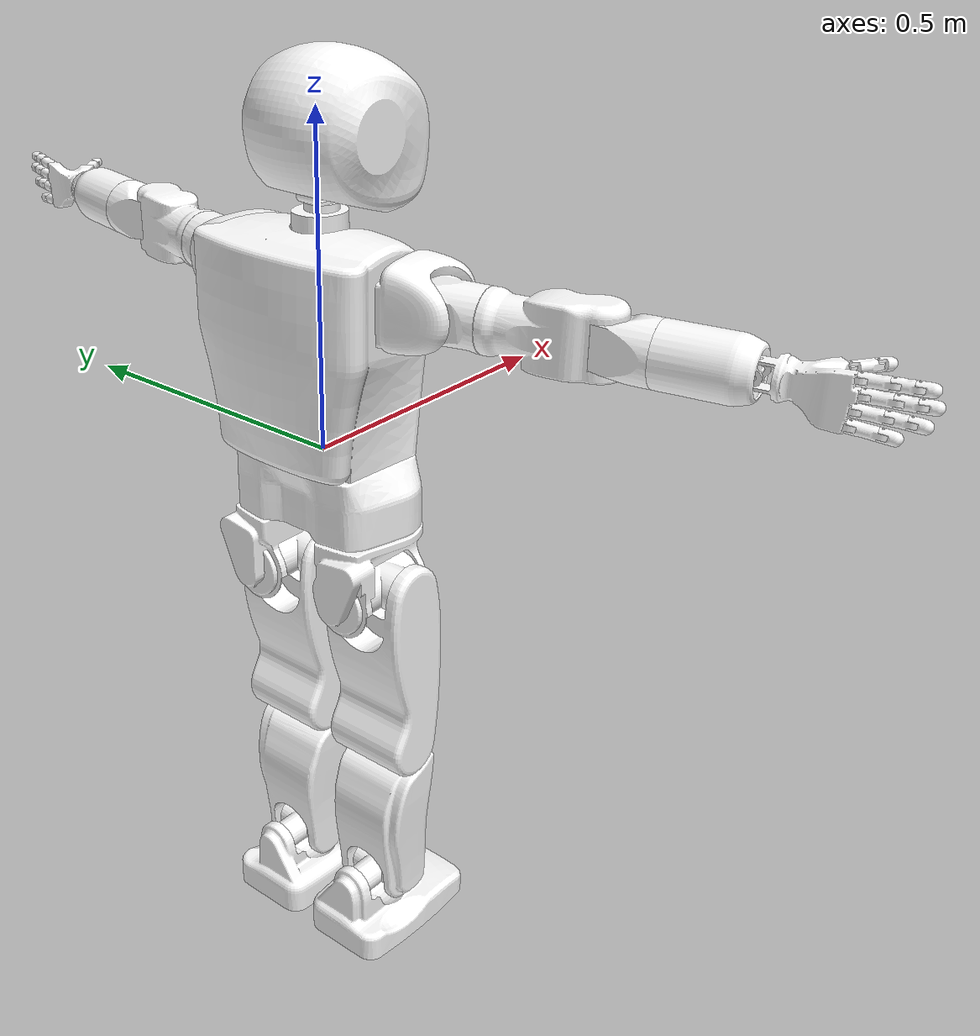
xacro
<?xml version="1.0"?>
<robot name="ar601" xmlns:xacro="http://www.ros.org/wiki/xacro">

    <xacro:include filename="$(find ar601_description)/urdf/common.xacro"/>
    <xacro:include filename="$(find ar601_description)/urdf/helper_macros.urdf.xacro"/>

    <xacro:include filename="$(find ar601_description)/urdf/ar601_primitive_collision_geoms.urdf.xacro"/>

    <xacro:include filename="$(find ar601_description)/urdf/ar601_original_inertia.urdf.xacro"/>
    <!-- NOT FIXED: -->
    <xacro:include filename="$(find ar601_description)/urdf/arm/ar601_arm.urdf.xacro"/>
    <xacro:include filename="$(find ar601_description)/urdf/arm/ar601_wrist.urdf.xacro"/>
    <!-- FIXED: -->
    <xacro:include filename="$(find ar601_description)/urdf/leg/ar601_leg_fixed.urdf.xacro"/>
    <xacro:include filename="$(find ar601_description)/urdf/torso/ar601_torso_fixed_no_collision.urdf.xacro"/>
    <xacro:include filename="$(find ar601_description)/urdf/head/ar601_head_fixed_no_collision.urdf.xacro"/>

    <ar601_torso_macro/>
    <ar601_arm_macro/>
    <ar601_wrist_macro/>
    <ar601_head_macro/>
    <ar601_leg_macro/>

    <xacro:include filename="$(find ar601_description)/gazebo/gazebo.urdf.xacro"/>

</robot>

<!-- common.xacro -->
<robot xmlns:xacro="http://www.ros.org/wiki/xacro">

  <!-- Joint dynamics -->

  <xacro:property name="leg_joint_friction"   value="0.1" />
  <xacro:property name="leg_joint_damping"  value="10.0" /> <!-- seems proper 10-20 -->
  <xacro:property name="arm_joint_friction"   value="1" />
  <xacro:property name="arm_joint_damping"  value="15" />
  <xacro:property name="head_joint_friction"   value="100.0" />
  <xacro:property name="head_joint_damping"  value="0.0" />
  <xacro:property name="torso_joint_friction"   value="100.0" />
  <xacro:property name="torso_joint_damping"  value="0.0" />
  <xacro:property name="wrist_joint_friction"   value="100.0" />
  <xacro:property name="wrist_joint_damping"  value="0.0" />

 <!--  NOMINAL EFFORT VALUES -->

<!--   STALL EFFORT VALUES -->

  <!--   30% STALL EFFORT VALUES -->

  <xacro:property name="hip_yaw_max_effort"  value="60.0" />
  <xacro:property name="hip_max_effort"  value="250.0" />
  <xacro:property name="knee_max_effort"  value="220.0" />
  <xacro:property name="ankle_max_effort"  value="60.0" />

    <!--   TEST STALL EFFORT VALUES -->

  <xacro:property name="ground_kp"  value="1000000.0" />
  <xacro:property name="ground_kd"  value="10000.0" />
  <xacro:property name="ground_mu1"  value="1.5" />
  <xacro:property name="ground_mu2"  value="1.5" />

</robot>

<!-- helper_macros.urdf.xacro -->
<robot  name="ar601" xmlns:xacro="http://www.ros.org/wiki/xacro">

   <xacro:macro name="joint_transmission_macro" params="joint_name">
    <transmission name="${joint_name}_transmssion">
      <type>transmission_interface/SimpleTransmission</type>
      <joint name="${joint_name}">
        <hardwareInterface>hardware_interface/EffortJointInterface</hardwareInterface>
      </joint>
      <actuator name="${joint_name}_motor">
        <hardwareInterface>EffortJointInterface</hardwareInterface>
        <mechanicalReduction>1</mechanicalReduction>
      </actuator>
    </transmission>
    <gazebo reference="${joint_name}">
      <implicitSpringDamper>1</implicitSpringDamper>
    </gazebo>
  </xacro:macro>

  <xacro:macro name="inertial_constant_macro" >
    <inertial>
      <mass value="0.5" />
      <origin xyz="0 0 0" />
      <inertia ixx="0.1" ixy="0.0" ixz="0.0"
               iyy="0.1" iyz="0.0"
               izz="0.1" />
    </inertial>
  </xacro:macro>

  <xacro:macro name="inertial_cuboid_macro" params="mass x_length y_length z_length">
    <inertial>
      <mass value="${mass}" />
      <origin xyz="0 0 0" />
      <inertia ixx="${(1/12) * mass* (y_length*y_length+ z_length*z_length)}" ixy="0.0" ixz="0.0"
               iyy="${(1/12) * mass* (x_length*x_length+ z_length*z_length)}" iyz="0.0"
               izz="${(1/12) * mass* (x_length*x_length+ y_length*y_length)}" />
    </inertial>
  </xacro:macro>

  <xacro:macro name="inertial_cuboid__with_pose_macro" params="mass x_length y_length z_length *origin">
    <inertial>
      <xacro:insert_block name="origin"/>
      <mass value="${mass}" />
      <inertia ixx="${(1/12) * mass* (y_length*y_length+ z_length*z_length)}" ixy="0.0" ixz="0.0"
               iyy="${(1/12) * mass* (x_length*x_length+ z_length*z_length)}" iyz="0.0"
               izz="${(1/12) * mass* (x_length*x_length+ y_length*y_length)}" />
    </inertial>
  </xacro:macro>

  <xacro:macro name="inertial_sphere_macro" params="mass diameter">
    <inertial>
      <mass value="${mass}" />
      <origin xyz="0 0 0" />
      <inertia ixx="${(2/5) * mass* ( (diameter*0.5)) * (diameter*0.5))}" ixy="0.0" ixz="0.0"
               iyy="${(2/5) * mass* ( (diameter*0.5)) * (diameter*0.5))}" iyz="0.0"
               izz="${(2/5) * mass* ( (diameter*0.5)) * (diameter*0.5))}" />
    </inertial>
  </xacro:macro>

  <xacro:macro name="inertial_sphere_with_pose_macro" params="mass diameter *origin">
    <inertial>
      <xacro:insert_block name="origin"/>
      <mass value="${mass}" />
      <inertia ixx="${(2/5) * mass* ( (diameter*0.5)) * (diameter*0.5))}" ixy="0.0" ixz="0.0"
               iyy="${(2/5) * mass* ( (diameter*0.5)) * (diameter*0.5))}" iyz="0.0"
               izz="${(2/5) * mass* ( (diameter*0.5)) * (diameter*0.5))}" />
    </inertial>
  </xacro:macro>

  <xacro:macro name="visual_macro" params="name">
    <visual>
      <origin
        xyz="0 0 0"
        rpy="0 0 0" />
      <geometry>
        <mesh
          filename="package://ar601_description/meshes/${name}.STL" />
      </geometry>
      <material
        name="">
        <color
          rgba="1 1 1 1" />
      </material>
    </visual>
  </xacro:macro>

  <xacro:macro name="collision_mesh_macro" params="name">
      <collision>
      <origin
        xyz="0 0 0"
        rpy="0 0 0" />
      <geometry>
        <mesh
          filename="package://ar601_description/meshes/${name}.STL" />
      </geometry>
    </collision>
  </xacro:macro>

  <xacro:macro name="link_macro" params="name">
    <link
      name="${name}">
      <xacro:call macro="${name}_inertial_macro"/>
      <xacro:call macro="${name}_collision_geom_macro"/>
      <visual_macro name="${name}" />
    </link>
  </xacro:macro>

  <xacro:macro name="link_macro_2" params="name">
    <link
      name="${name}">
      <xacro:call macro="${name}_inertial_macro"/>
      <visual_macro name="${name}" />
    </link>
  </xacro:macro>

</robot>

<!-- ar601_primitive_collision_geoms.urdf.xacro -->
<robot name="ar601" xmlns:xacro="http://www.ros.org/wiki/xacro">

  <xacro:include filename="$(find ar601_description)/urdf/head/ar601_head_primitive_collision_geoms.urdf.xacro" />
  <xacro:include filename="$(find ar601_description)/urdf/leg/ar601_leg_primitive_collision_geoms.urdf.xacro" />
  <xacro:include filename="$(find ar601_description)/urdf/arm/ar601_arm_primitive_collision_geoms.urdf.xacro" />
  <xacro:include filename="$(find ar601_description)/urdf/arm/ar601_wrist_primitive_collision_geoms.urdf.xacro" />
  <xacro:include filename="$(find ar601_description)/urdf/torso/ar601_torso_primitive_collision_geoms.urdf.xacro" />

</robot>

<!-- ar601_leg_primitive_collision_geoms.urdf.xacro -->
<robot  name="robotis_op2" xmlns:xacro="http://www.ros.org/wiki/xacro">

<xacro:macro name="LPelvis_collision_geom_macro">
    <collision>
      <origin xyz="0.000000 -0.010580 0.028437" />
      <geometry>
        <box size="0.045 0.08175 0.028652" />
      </geometry>
    </collision>
</xacro:macro>

<xacro:macro name="LHip_collision_geom_macro">
    <collision>
      <origin xyz="0.000079 0.018242 0.013873" />
      <geometry>
        <box size="0.001 0.001 0.001"/>
      </geometry>
    </collision>
</xacro:macro>

<xacro:macro name="LThigh_collision_geom_macro">
    <collision>
      <origin xyz="-0.062965 -0.000323 0.000692" />
      <geometry>
        <box size="0.093 0.035 0.045"/>
      </geometry>
    </collision>
</xacro:macro>

<xacro:macro name="LTibia_collision_geom_macro">
    <collision>
      <origin xyz="-0.053955 0.006548 -0.000592" />
      <geometry>
        <box size="0.093 0.035 0.045"/>
      </geometry>
    </collision>
</xacro:macro>

<xacro:macro name="LAnkle_collision_geom_macro">
    <collision>
      <origin xyz="-0.000214 -0.018536 0.013873" />
      <geometry>
        <box size="0.028652 0.08175 0.045"/>
      </geometry>
    </collision>
</xacro:macro>

<xacro:macro name="LFoot_collision_geom_macro">
    <collision>
      <origin xyz="0.02 0 -0.05275" />
      <geometry>
        <box size="0.234 0.134 0.1055"/>
      </geometry>
    </collision>
</xacro:macro>

<xacro:macro name="RPelvis_collision_geom_macro">
    <collision>
      <origin xyz="0.000000 0.010580 0.028437" />
      <geometry>
        <box size="0.045 0.08175 0.028652" />
      </geometry>
    </collision>
</xacro:macro>

<xacro:macro name="RHip_collision_geom_macro">
    <collision>
      <origin xyz="0.000079 -0.018242 0.0138735" />
      <geometry>
        <box size="0.001 0.001 0.001"/>
      </geometry>
    </collision>
</xacro:macro>

<xacro:macro name="RThigh_collision_geom_macro">
    <collision>
      <origin xyz="0.062965 -0.000323 0.000692" />
      <geometry>
        <box size="0.093 0.035 0.045"/>
      </geometry>
    </collision>
</xacro:macro>

<xacro:macro name="RTibia_collision_geom_macro">
    <collision>
      <origin xyz="0.053955 0.006548 -0.000592" />
      <geometry>
        <box size="0.093 0.035 0.045"/>
      </geometry>
    </collision>
</xacro:macro>

<xacro:macro name="RAnkle_collision_geom_macro">
    <collision>
      <origin xyz="-0.000214 -0.018536 0.013873" />
      <geometry>
        <box size="0.028652 0.08175 0.045"/>
      </geometry>
    </collision>
</xacro:macro>

<xacro:macro name="RFoot_collision_geom_macro">
    <collision>
      <origin xyz="0.02 0 -0.05275" />
      <geometry>
        <box size="0.234 0.134 0.1055"/>
      </geometry>
    </collision>
</xacro:macro>

</robot>

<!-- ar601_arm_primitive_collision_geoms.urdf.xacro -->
<robot  name="ar601" xmlns:xacro="http://www.ros.org/wiki/xacro">

<xacro:macro name="LShoulder1_collision_geom_macro">
    <collision>
      <origin xyz="-0.0031158909 0.020443695 -0.019663084" />
      <geometry>
        <box size="0.001 0.001 0.001"  scale="1 1 1"/>
      </geometry>
    </collision>
</xacro:macro>

<xacro:macro name="RShoulder1_collision_geom_macro">
    <collision>
      <origin xyz="-0.013522619 -0.010264050 0.0013935747" />
      <geometry>
        <box size="0.016 0.033 0.02165" />
      </geometry>
    </collision>
</xacro:macro>

<xacro:macro name="LShoulder2_collision_geom_macro">
    <collision>
      <origin xyz="-0.036239 0.000734 0.000660" />
      <geometry>
        <box size="0.06 0.032 0.035" />
      </geometry>
    </collision>
</xacro:macro>

<xacro:macro name="RShoulder2_collision_geom_macro">
    <collision>
      <origin xyz="0.016 0.016 0" rpy="0 0 0" />
      <geometry>
        <box size="0.032 0.032 0.035" />
      </geometry>
    </collision>
</xacro:macro>

<xacro:macro name="LShoulder3_collision_geom_macro">
    <collision>
      <origin xyz="0.016 0 0" rpy="0 0 0" />
      <geometry>
        <box size="0.064 0.032 0.032" />
      </geometry>
    </collision>
</xacro:macro>

<xacro:macro name="RShoulder3_collision_geom_macro">
    <collision>
      <geometry>
        <box size="0.032 0.005 0.032" />
      </geometry>
    </collision>
</xacro:macro>

<xacro:macro name="LElbow_collision_geom_macro">
    <collision>
      <origin xyz="0.016 0 0" rpy="0 0 0" />
      <geometry>
        <box size="0.032 0.005 0.032" />
      </geometry>
    </collision>
</xacro:macro>

<xacro:macro name="RElbow_collision_geom_macro">
    <collision>
      <geometry>
        <box size="0.001 0.001 0.001" />
      </geometry>
    </collision>
</xacro:macro>

<xacro:macro name="LArm_collision_geom_macro">
    <collision>
      <origin xyz="-0.013523 0.010264 0.001394" />
      <geometry>
        <box size="0.016 0.033 0.02165" />
      </geometry>
    </collision>
</xacro:macro>

<xacro:macro name="RArm_collision_geom_macro">
    <collision>
      <origin xyz="-0.036239 0.000734 -0.000660" />
      <geometry>
        <box size="0.06 0.032 0.035"/>
      </geometry>
    </collision>
</xacro:macro>

</robot>

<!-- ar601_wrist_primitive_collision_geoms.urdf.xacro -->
<robot  name="ar601" xmlns:xacro="http://www.ros.org/wiki/xacro">

<xacro:macro name="LWrist1_collision_geom_macro">
    <collision>
      <origin xyz="-0.0031158909 0.020443695 -0.019663084" />
      <geometry>
        <box size="0.001 0.001 0.001"  scale="1 1 1"/>
      </geometry>
    </collision>
</xacro:macro>

<xacro:macro name="RWrist1_collision_geom_macro">
    <collision>
      <origin xyz="-0.013522619 -0.010264050 0.0013935747" />
      <geometry>
        <box size="0.016 0.033 0.02165" />
      </geometry>
    </collision>
</xacro:macro>

<xacro:macro name="LWrist2_collision_geom_macro">
    <collision>
      <origin xyz="-0.036239 0.000734 0.000660" />
      <geometry>
        <box size="0.06 0.032 0.035" />
      </geometry>
    </collision>
</xacro:macro>

<xacro:macro name="RWrist2_collision_geom_macro">
    <collision>
      <origin xyz="0.016 0.016 0" rpy="0 0 0" />
      <geometry>
        <box size="0.032 0.032 0.035" />
      </geometry>
    </collision>
</xacro:macro>

<xacro:macro name="LFinger1_1_collision_geom_macro">
    <collision>
      <origin xyz="0.016 0 0" rpy="0 0 0" />
      <geometry>
        <box size="0.064 0.032 0.032" />
      </geometry>
    </collision>
</xacro:macro>

<xacro:macro name="RFinger1_1_collision_geom_macro">
    <collision>
      <geometry>
        <box size="0.032 0.005 0.032" />
      </geometry>
    </collision>
</xacro:macro>

<xacro:macro name="LFinger1_2_collision_geom_macro">
    <collision>
      <origin xyz="0.016 0 0" rpy="0 0 0" />
      <geometry>
        <box size="0.032 0.005 0.032" />
      </geometry>
    </collision>
</xacro:macro>

<xacro:macro name="RFinger1_2_collision_geom_macro">
    <collision>
      <geometry>
        <box size="0.001 0.001 0.001" />
      </geometry>
    </collision>
</xacro:macro>

<xacro:macro name="LFinger2_1_collision_geom_macro">
    <collision>
      <origin xyz="-0.013523 0.010264 0.001394" />
      <geometry>
        <box size="0.016 0.033 0.02165" />
      </geometry>
    </collision>
</xacro:macro>

<xacro:macro name="RFinger2_1_collision_geom_macro">
    <collision>
      <origin xyz="-0.036239 0.000734 -0.000660" />
      <geometry>
        <box size="0.06 0.032 0.035"/>
      </geometry>
    </collision>
</xacro:macro>

<xacro:macro name="LFinger2_2_collision_geom_macro">
    <collision>
      <origin xyz="-0.036239 0.000734 -0.000660" />
      <geometry>
        <box size="0.06 0.032 0.035"/>
      </geometry>
    </collision>
</xacro:macro>

<xacro:macro name="RFinger2_2_collision_geom_macro">
    <collision>
      <origin xyz="-0.036239 0.000734 -0.000660" />
      <geometry>
        <box size="0.06 0.032 0.035"/>
      </geometry>
    </collision>
</xacro:macro>

<xacro:macro name="LFinger2_3_collision_geom_macro">
    <collision>
      <origin xyz="-0.036239 0.000734 -0.000660" />
      <geometry>
        <box size="0.06 0.032 0.035"/>
      </geometry>
    </collision>
</xacro:macro>

<xacro:macro name="RFinger2_3_collision_geom_macro">
    <collision>
      <origin xyz="-0.036239 0.000734 -0.000660" />
      <geometry>
        <box size="0.06 0.032 0.035"/>
      </geometry>
    </collision>
</xacro:macro>

<xacro:macro name="LFinger3_1_collision_geom_macro">
    <collision>
      <origin xyz="-0.036239 0.000734 -0.000660" />
      <geometry>
        <box size="0.06 0.032 0.035"/>
      </geometry>
    </collision>
</xacro:macro>

<xacro:macro name="RFinger3_1_collision_geom_macro">
    <collision>
      <origin xyz="-0.036239 0.000734 -0.000660" />
      <geometry>
        <box size="0.06 0.032 0.035"/>
      </geometry>
    </collision>
</xacro:macro>

<xacro:macro name="LFinger3_2_collision_geom_macro">
    <collision>
      <origin xyz="-0.036239 0.000734 -0.000660" />
      <geometry>
        <box size="0.06 0.032 0.035"/>
      </geometry>
    </collision>
</xacro:macro>

<xacro:macro name="RFinger3_2_collision_geom_macro">
    <collision>
      <origin xyz="-0.036239 0.000734 -0.000660" />
      <geometry>
        <box size="0.06 0.032 0.035"/>
      </geometry>
    </collision>
</xacro:macro>

<xacro:macro name="LFinger3_3_collision_geom_macro">
    <collision>
      <origin xyz="-0.036239 0.000734 -0.000660" />
      <geometry>
        <box size="0.06 0.032 0.035"/>
      </geometry>
    </collision>
</xacro:macro>

<xacro:macro name="RFinger3_3_collision_geom_macro">
    <collision>
      <origin xyz="-0.036239 0.000734 -0.000660" />
      <geometry>
        <box size="0.06 0.032 0.035"/>
      </geometry>
    </collision>
</xacro:macro>

<xacro:macro name="LFinger4_1_collision_geom_macro">
    <collision>
      <origin xyz="-0.036239 0.000734 -0.000660" />
      <geometry>
        <box size="0.06 0.032 0.035"/>
      </geometry>
    </collision>
</xacro:macro>

<xacro:macro name="RFinger4_1_collision_geom_macro">
    <collision>
      <origin xyz="-0.036239 0.000734 -0.000660" />
      <geometry>
        <box size="0.06 0.032 0.035"/>
      </geometry>
    </collision>
</xacro:macro>

<xacro:macro name="LFinger4_2_collision_geom_macro">
    <collision>
      <origin xyz="-0.036239 0.000734 -0.000660" />
      <geometry>
        <box size="0.06 0.032 0.035"/>
      </geometry>
    </collision>
</xacro:macro>

<xacro:macro name="RFinger4_2_collision_geom_macro">
    <collision>
      <origin xyz="-0.036239 0.000734 -0.000660" />
      <geometry>
        <box size="0.06 0.032 0.035"/>
      </geometry>
    </collision>
</xacro:macro>

<xacro:macro name="LFinger4_3_collision_geom_macro">
    <collision>
      <origin xyz="-0.036239 0.000734 -0.000660" />
      <geometry>
        <box size="0.06 0.032 0.035"/>
      </geometry>
    </collision>
</xacro:macro>

<xacro:macro name="RFinger4_3_collision_geom_macro">
    <collision>
      <origin xyz="-0.036239 0.000734 -0.000660" />
      <geometry>
        <box size="0.06 0.032 0.035"/>
      </geometry>
    </collision>
</xacro:macro>

<xacro:macro name="LFinger5_1_collision_geom_macro">
    <collision>
      <origin xyz="-0.036239 0.000734 -0.000660" />
      <geometry>
        <box size="0.06 0.032 0.035"/>
      </geometry>
    </collision>
</xacro:macro>

<xacro:macro name="RFinger5_1_collision_geom_macro">
    <collision>
      <origin xyz="-0.036239 0.000734 -0.000660" />
      <geometry>
        <box size="0.06 0.032 0.035"/>
      </geometry>
    </collision>
</xacro:macro>

<xacro:macro name="LFinger5_2_collision_geom_macro">
    <collision>
      <origin xyz="-0.036239 0.000734 -0.000660" />
      <geometry>
        <box size="0.06 0.032 0.035"/>
      </geometry>
    </collision>
</xacro:macro>

<xacro:macro name="RFinger5_2_collision_geom_macro">
    <collision>
      <origin xyz="-0.036239 0.000734 -0.000660" />
      <geometry>
        <box size="0.06 0.032 0.035"/>
      </geometry>
    </collision>
</xacro:macro>

</robot>

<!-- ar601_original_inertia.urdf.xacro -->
<robot name="ar601" xmlns:xacro="http://www.ros.org/wiki/xacro">

  <xacro:include filename="$(find ar601_description)/urdf/head/ar601_head_original_inertia.urdf.xacro" />
  <xacro:include filename="$(find ar601_description)/urdf/leg/ar601_leg_original_inertia.urdf.xacro" />
  <xacro:include filename="$(find ar601_description)/urdf/arm/ar601_arm_original_inertia.urdf.xacro" />
  <xacro:include filename="$(find ar601_description)/urdf/arm/ar601_wrist_original_inertia.urdf.xacro" />
  <xacro:include filename="$(find ar601_description)/urdf/torso/ar601_torso_original_inertia.urdf.xacro" />

</robot>

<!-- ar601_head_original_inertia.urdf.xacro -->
<robot  name="robotis_op2" xmlns:xacro="http://www.ros.org/wiki/xacro">

<xacro:macro name="Neck1_inertial_macro">
    <inertial>
      <origin
        xyz="-0.0222927487404251 4.47895651753766E-05 0.0310409976295018"
        rpy="0 0 0" />
      <mass
        value="0.657320428434859" />
      <inertia
        ixx="0.00102025512184757"
        ixy="0.0"
        ixz="0.0"
        iyy="0.00120134781263084"
        iyz="0.0"
        izz="0.000718372081172033" />
    </inertial>
</xacro:macro>

<xacro:macro name="Neck2_inertial_macro">
    <inertial>
      <origin
        xyz="-9.38630904016337E-06 4.42165265520866E-05 -0.0162910790688592"
        rpy="0 0 0" />
      <mass
        value="0.0167205530633327" />
      <inertia
        ixx="6.21421984464677E-06"
        ixy="0.0"
        ixz="0.0"
        iyy="1.28553666419653E-05"
        iyz="0.0"
        izz="1.23400064727747E-05" />
    </inertial>
</xacro:macro>

<xacro:macro name="Head1_inertial_macro">
    <inertial>
      <origin
        xyz="-9.38941181994821E-06 4.42605420928731E-05 -2.87270207621759E-13"
        rpy="0 0 0" />
      <mass
        value="0.140258674510404" />
      <inertia
        ixx="0.000255527506833601"
        ixy="0.0"
        ixz="0.0"
        iyy="2.64614495249746E-05"
        iyz="0.0"
        izz="0.000265796055755356" />
    </inertial>
</xacro:macro>

<xacro:macro name="Head2_inertial_macro">
    <inertial>
      <origin
        xyz="0.0367567218407244 6.13069479271212E-05 0.0741939345619121"
        rpy="0 0 0" />
      <mass
        value="5.51543814682702" />
      <inertia
        ixx="0.0328094469174202"
        ixy="0.0"
        ixz="0.0"
        iyy="0.0336400080305931"
        iyz="0.0"
        izz="0.0379699861871773" />
    </inertial>
</xacro:macro>

</robot>

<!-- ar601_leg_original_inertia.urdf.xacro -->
<robot  name="robotis_op2" xmlns:xacro="http://www.ros.org/wiki/xacro">

<xacro:macro name="LPelvis_inertial_macro">
    <inertial>
      <origin
        xyz="-0.034 0.0 0.054"
        rpy="0 0 0" />
      <mass
        value="0.908" />
      <inertia
        ixx="0.00151"
        ixy="0.0"
        ixz="0.0"
        iyy="0.00414"
        iyz="0.0"
        izz="0.0037" />
    </inertial>
</xacro:macro>

<xacro:macro name="RPelvis_inertial_macro">
    <inertial>
      <origin
        xyz="-0.034 0.0 0.054"
        rpy="0 0 0" />
      <mass
        value="0.908" />
      <inertia
        ixx="0.00151"
        ixy="0.0"
        ixz="0.0"
        iyy="0.00414"
        iyz="0.0"
        izz="0.0037" />
    </inertial>
</xacro:macro>

<xacro:macro name="LHip_inertial_macro">
    <inertial>
      <origin
        xyz="-0.014 0.0 0.0"
        rpy="0 0 0" />
      <mass
        value="0.755" />
      <inertia
        ixx="0.000786"
        ixy="0.0"
        ixz="0.0"
        iyy="0.00127"
        iyz="0.0"
        izz="0.00156" />
    </inertial>
</xacro:macro>

<xacro:macro name="RHip_inertial_macro">
    <inertial>
      <origin
        xyz="-0.014 0.0 0.0"
        rpy="0 0 0" />
      <mass
        value="0.755" />
      <inertia
        ixx="0.000786"
        ixy="0.0"
        ixz="0.0"
        iyy="0.00127"
        iyz="0.0"
        izz="0.00156" />
    </inertial>
</xacro:macro>

<xacro:macro name="LThigh_inertial_macro">
    <inertial>
      <origin
        xyz="0.008 0.007 -0.17"
        rpy="0 0 0" />
      <mass
        value="4.04" />
      <inertia
        ixx="0.0407"
        ixy="0.0"
        ixz="0.0"
        iyy="0.0352"
        iyz="0.0"
        izz="0.0117" />
    </inertial>
</xacro:macro>

<xacro:macro name="RThigh_inertial_macro">
    <inertial>
      <origin
        xyz="0.008 -0.007 -0.17"
        rpy="0 0 0" />
      <mass
        value="4.04" />
      <inertia
        ixx="0.0407"
        ixy="0.0"
        ixz="0.0"
        iyy="0.0352"
        iyz="0.0"
        izz="0.0117" />
    </inertial>
</xacro:macro>

<xacro:macro name="LTibia_inertial_macro">
    <inertial>
      <origin
        xyz="0.002 0.004 -0.153"
        rpy="0 0 0" />
      <mass
        value="2.441" />
      <inertia
        ixx="0.0138"
        ixy="0.0"
        ixz="0.0"
        iyy="0.0113"
        iyz="0.0"
        izz="0.00566" />
    </inertial>
</xacro:macro>

<xacro:macro name="RTibia_inertial_macro">
    <inertial>
      <origin
        xyz="0.002 -0.004 -0.153"
        rpy="0 0 0" />
      <mass
        value="2.441" />
      <inertia
        ixx="0.0138"
        ixy="0.0"
        ixz="0.0"
        iyy="0.0113"
        iyz="0.0"
        izz="0.00566" />
    </inertial>
</xacro:macro>

<xacro:macro name="LAnkle_inertial_macro">
    <inertial>
      <origin
        xyz="-0.007 -0.001 0.0"
        rpy="0 0 0" />
      <mass
        value="0.297" />
      <inertia
        ixx="0.000161"
        ixy="0.0"
        ixz="0.0"
        iyy="0.000283"
        iyz="0.0"
        izz="0.000346" />
    </inertial>
</xacro:macro>

<xacro:macro name="RAnkle_inertial_macro">
    <inertial>
      <origin
        xyz="-0.007 0.001 0.0"
        rpy="0 0 0" />
      <mass
        value="0.297" />
      <inertia
        ixx="0.000161"
        ixy="0.0"
        ixz="0.0"
        iyy="0.000283"
        iyz="0.0"
        izz="0.000346" />
    </inertial>
</xacro:macro>

<xacro:macro name="LFoot_inertial_macro">
    <inertial>
      <origin
        xyz="0.008 -0.004 -0.072"
        rpy="0 0 0" />
      <mass
        value="2.208" />
      <inertia
        ixx="0.00541"
        ixy="0.0"
        ixz="0.0"
        iyy="0.0129"
        iyz="0.0"
        izz="0.0152" />
    </inertial>
</xacro:macro>

<xacro:macro name="RFoot_inertial_macro">
    <inertial>
      <origin
        xyz="0.008 0.004 -0.072"
        rpy="0 0 0" />
      <mass
        value="2.208" />
      <inertia
        ixx="0.00541"
        ixy="0.0"
        ixz="0.0"
        iyy="0.0129"
        iyz="0.0"
        izz="0.0152" />
    </inertial>
</xacro:macro>

</robot>

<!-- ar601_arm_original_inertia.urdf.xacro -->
<robot  name="ar601" xmlns:xacro="http://www.ros.org/wiki/xacro">

<xacro:macro name="LShoulder1_inertial_macro">
    <inertial>
      <origin
        xyz="0.0119 0.0447 0.0125"
        rpy="0 0 0" />
      <mass
        value="0.702" />
      <inertia
        ixx="0.00107"
        ixy="0.0"
        ixz="0.0"
        iyy="0.00208"
        iyz="0.0"
        izz="0.00181" />
    </inertial>
</xacro:macro>

<xacro:macro name="RShoulder1_inertial_macro">
    <inertial>
      <origin
        xyz="0.0119 -0.0447 0.0125"
        rpy="0 0 0" />
      <mass
        value="0.702" />
      <inertia
        ixx="0.00107"
        ixy="0.0"
        ixz="0.0"
        iyy="0.00208"
        iyz="0.0"
        izz="0.00181" />
    </inertial>
</xacro:macro>

<xacro:macro name="LShoulder2_inertial_macro">
    <inertial>
      <origin
        xyz="0.0512 0.0264 0.00120"
        rpy="0 0 0" />
      <mass
        value="0.710" />
      <inertia
        ixx="0.00114"
        ixy="0.0"
        ixz="0.0"
        iyy="0.000678"
        iyz="0.0"
        izz="0.00118" />
    </inertial>
</xacro:macro>

<xacro:macro name="RShoulder2_inertial_macro">
    <inertial>
      <origin
        xyz="0.0512 -0.0264 0.00120"
        rpy="0 0 0" />
      <mass
        value="0.710" />
      <inertia
        ixx="0.00114"
        ixy="0.0"
        ixz="0.0"
        iyy="0.000678"
        iyz="0.0"
        izz="0.00118" />
    </inertial>
</xacro:macro>

<xacro:macro name="LShoulder3_inertial_macro">
    <inertial>
      <origin
        xyz="0 0.0754 0"
        rpy="0 0 0" />
      <mass
        value="0.924" />
      <inertia
        ixx="0.00281"
        ixy="0.0"
        ixz="0.0"
        iyy="0.00111"
        iyz="0.0"
        izz="0.00248" />
    </inertial>
</xacro:macro>

<xacro:macro name="RShoulder3_inertial_macro">
    <inertial>
      <origin
        xyz="0 -0.0754 0"
        rpy="0 0 0" />
      <mass
        value="0.923986049465604" />
      <inertia
        ixx="0.00281"
        ixy="0.0"
        ixz="0.0"
        iyy="0.00111"
        iyz="0.0"
        izz="0.00248" />
    </inertial>
</xacro:macro>

<xacro:macro name="LElbow_inertial_macro">
    <inertial>
      <origin
        xyz="-0.006 0.0268 -0.0306"
        rpy="0 0 0" />
      <mass
        value="0.067" />
      <inertia
        ixx="0.000109"
        ixy="0.0"
        ixz="0.0"
        iyy="8.7E-05"
        iyz="0.0"
        izz="0.000124" />
    </inertial>
</xacro:macro>

<xacro:macro name="RElbow_inertial_macro">
    <inertial>
      <origin
        xyz="-0.006 -0.0268 -0.0306"
        rpy="0 0 0" />
      <mass
        value="0.067" />
      <inertia
        ixx="0.000109"
        ixy="0.0"
        ixz="0.0"
        iyy="8.7E-05"
        iyz="0.0"
        izz="0.000124" />
    </inertial>
</xacro:macro>

<xacro:macro name="LArm_inertial_macro">
    <inertial>
      <origin
        xyz="0 0.0546 0.0003"
        rpy="0 0 0" />
      <mass
        value="0.698" />
      <inertia
        ixx="0.00106"
        ixy="0.0"
        ixz="0.0"
        iyy="0.000705"
        iyz="0.0"
        izz="0.00107" />
    </inertial>
</xacro:macro>

<xacro:macro name="RArm_inertial_macro">
    <inertial>
      <origin
        xyz="0 -0.0546 0.0003"
        rpy="0 0 0" />
      <mass
        value="0.698" />
      <inertia
        ixx="0.00106"
        ixy="0.0"
        ixz="0.0"
        iyy="0.000705"
        iyz="0.0"
        izz="0.00107" />
    </inertial>
</xacro:macro>

</robot>

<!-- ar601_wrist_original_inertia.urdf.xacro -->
<robot  name="ar601" xmlns:xacro="http://www.ros.org/wiki/xacro">

<xacro:macro name="LWrist1_inertial_macro">
    <inertial>
      <origin
        xyz="8.69257801849876E-09 0 -8.69257799074319E-09"
        rpy="0 0 0" />
      <mass
        value="0.00354841244692992" />
      <inertia
        ixx="0"
        ixy="0.0"
        ixz="0.0"
        iyy="0"
        iyz="0.0"
        izz="0" />
    </inertial>
</xacro:macro>

<xacro:macro name="RWrist1_inertial_macro">
    <inertial>
      <origin
        xyz="-8.69257804625434E-09 -1.11022302462516E-16 -8.69257799074319E-09"
        rpy="0 0 0" />
      <mass
        value="0.00354841244692995" />
      <inertia
        ixx="0"
        ixy="0.0"
        ixz="0.0"
        iyy="0"
        iyz="0.0"
        izz="0" />
    </inertial>
</xacro:macro>

<xacro:macro name="LWrist2_inertial_macro">
    <inertial>
      <origin
        xyz="-0.00320146376134629 0.0679998358897447 -0.00139578498789278"
        rpy="0 0 0" />
      <mass
        value="0.106503207491186" />
      <inertia
        ixx="0.000160140258431206"
        ixy="0.0"
        ixz="0.0"
        iyy="7.18787865803972E-05"
        iyz="0.0"
        izz="0.000161242457643774" />
    </inertial>
</xacro:macro>

<xacro:macro name="RWrist2_inertial_macro">
    <inertial>
      <origin
        xyz="-0.0032015407111433 -0.0680002451287101 -0.00139605167258255"
        rpy="0 0 0" />
      <mass
        value="0.106500992906003" />
      <inertia
        ixx="0.000160137434624347"
        ixy="0.0"
        ixz="0.0"
        iyy="7.18756092477474E-05"
        iyz="0.0"
        izz="0.000161241258582528" />
    </inertial>
</xacro:macro>

<xacro:macro name="LFinger1_1_inertial_macro">
    <inertial>
      <origin
        xyz="0.017392149570403 0.0125768799508672 -0.00399999938736578"
        rpy="0 0 0" />
      <mass
        value="0.00794971429092078" />
      <inertia
        ixx="6.15322908627996E-07"
        ixy="0.0"
        ixz="0.0"
        iyy="8.19342049389076E-07"
        iyz="0.0"
        izz="1.16701160817821E-06" />
    </inertial>
</xacro:macro>

<xacro:macro name="RFinger1_1_inertial_macro">
    <inertial>
      <origin
        xyz="0.018058 -0.011601 -0.004"
        rpy="0 0 0" />
      <mass
        value="0.0079497" />
      <inertia
        ixx="5.7022E-07"
        ixy="0.0"
        ixz="0.0"
        iyy="8.6444E-07"
        iyz="0.0"
        izz="1.167E-06" />
    </inertial>
</xacro:macro>

<xacro:macro name="LFinger1_2_inertial_macro">
    <inertial>
      <origin
        xyz="0.0105994545023848 0.00682969355090124 -0.00399999152754377"
        rpy="0 0 0" />
      <mass
        value="0.0041977190113557" />
      <inertia
        ixx="2.06802404520768E-07"
        ixy="0.0"
        ixz="0.0"
        iyy="2.21544071243177E-07"
        iyz="0.0"
        izz="2.61121380624231E-07" />
    </inertial>
</xacro:macro>

<xacro:macro name="RFinger1_2_inertial_macro">
    <inertial>
      <origin
        xyz="0.0104605997712183 -0.00704052558917401 -0.00400000848701126"
        rpy="0 0 0" />
      <mass
        value="0.00419771897410452" />
      <inertia
        ixx="2.09142237590012E-07"
        ixy="0.0"
        ixz="0.0"
        iyy="2.19204240697583E-07"
        iyz="0.0"
        izz="2.61121384273268E-07" />
    </inertial>
</xacro:macro>

<xacro:macro name="LFinger2_1_inertial_macro">
    <inertial>
      <origin
        xyz="0.00549196215025359 0.0208173591048728 -0.00362500054881426"
        rpy="0 0 0" />
      <mass
        value="0.00794969630364376" />
      <inertia
        ixx="1.07237570353924E-06"
        ixy="0.0"
        ixz="0.0"
        iyy="3.62556603064786E-07"
        iyz="0.0"
        izz="1.16674304524627E-06" />
    </inertial>
</xacro:macro>

<xacro:macro name="RFinger2_1_inertial_macro">
    <inertial>
      <origin
        xyz="0.00466411344108193 -0.0210181956784309 -0.00362576268809778"
        rpy="0 0 0" />
      <mass
        value="0.00794969377283116" />
      <inertia
        ixx="1.09026286614019E-06"
        ixy="0.0"
        ixz="0.0"
        iyy="3.44669160887216E-07"
        iyz="0.0"
        izz="1.16674314947762E-06" />
    </inertial>
</xacro:macro>

<xacro:macro name="LFinger2_2_inertial_macro">
    <inertial>
      <origin
        xyz="0.00506087231326857 0.0156875104338542 -0.00371293073598111"
        rpy="0 0 0" />
      <mass
        value="0.00554910902171019" />
      <inertia
        ixx="4.87095066933935E-07"
        ixy="0.0"
        ixz="0.0"
        iyy="2.47574406917102E-07"
        iyz="0.0"
        izz="5.45118280139522E-07" />
    </inertial>
</xacro:macro>

<xacro:macro name="RFinger2_2_inertial_macro">
    <inertial>
      <origin
        xyz="0.00340591071964673 -0.0161277265396876 -0.00371387542361651"
        rpy="0 0 0" />
      <mass
        value="0.00554910460160714" />
      <inertia
        ixx="5.08721761194374E-07"
        ixy="0.0"
        ixz="0.0"
        iyy="2.25948765171186E-07"
        iyz="0.0"
        izz="5.4511708567559E-07" />
    </inertial>
</xacro:macro>

<xacro:macro name="LFinger2_3_inertial_macro">
    <inertial>
      <origin
        xyz="0.00268001122286671 0.0123904174102188 -0.00377999084881703"
        rpy="0 0 0" />
      <mass
        value="0.00419771959929121" />
      <inertia
        ixx="2.58144318341166E-07"
        ixy="0.0"
        ixz="0.0"
        iyy="1.7023412529365E-07"
        iyz="0.0"
        izz="2.61089320284028E-07" />
    </inertial>
</xacro:macro>

<xacro:macro name="RFinger2_3_inertial_macro">
    <inertial>
      <origin
        xyz="0.00245171343968303 -0.0124374976484516 -0.00378032558892799"
        rpy="0 0 0" />
      <mass
        value="0.00419771964934734" />
      <inertia
        ixx="2.59555350116999E-07"
        ixy="0.0"
        ixz="0.0"
        iyy="1.6882316593225E-07"
        iyz="0.0"
        izz="2.61089184393434E-07" />
    </inertial>
</xacro:macro>

<xacro:macro name="LFinger3_1_inertial_macro">
    <inertial>
      <origin
        xyz="0.00486393266793878 0.0209047085521565 -0.00400000345690754"
        rpy="0 0 0" />
      <mass
        value="0.00794969171707417" />
      <inertia
        ixx="1.0857545480312E-06"
        ixy="0.0"
        ixz="0.0"
        iyy="3.48910305135014E-07"
        iyz="0.0"
        izz="1.16701018610524E-06" />
    </inertial>
</xacro:macro>

<xacro:macro name="RFinger3_1_inertial_macro">
    <inertial>
      <origin
        xyz="0.00455337847888747 -0.0209745421456283 -0.00399999638824711"
        rpy="0 0 0" />
      <mass
        value="0.00794969055324976" />
      <inertia
        ixx="1.09207369431954E-06"
        ixy="0.0"
        ixz="0.0"
        iyy="3.42591157593321E-07"
        iyz="0.0"
        izz="1.16701011250278E-06" />
    </inertial>
</xacro:macro>

<xacro:macro name="LFinger3_2_inertial_macro">
    <inertial>
      <origin
        xyz="0.00465559688611381 0.0157423591331163 -0.00399997065634744"
        rpy="0 0 0" />
      <mass
        value="0.00554910682396278" />
      <inertia
        ixx="4.92692912454704E-07"
        ixy="0.0"
        ixz="0.0"
        iyy="2.41872402469041E-07"
        iyz="0.0"
        izz="5.45222393521601E-07" />
    </inertial>
</xacro:macro>

<xacro:macro name="RFinger3_2_inertial_macro">
    <inertial>
      <origin
        xyz="0.00337177939747289 -0.0160663472035111 -0.00400002877010486"
        rpy="0 0 0" />
      <mass
        value="0.00554910281221021" />
      <inertia
        ixx="5.08879384138404E-07"
        ixy="0.0"
        ixz="0.0"
        iyy="2.25685955064701E-07"
        iyz="0.0"
        izz="5.45222208070927E-07" />
    </inertial>
</xacro:macro>

<xacro:macro name="LFinger3_3_inertial_macro">
    <inertial>
      <origin
        xyz="0.00345549223233155 0.0121265307317509 -0.00400000816255019"
        rpy="0 0 0" />
      <mass
        value="0.00419771963133254" />
      <inertia
        ixx="2.52716242601003E-07"
        ixy="0.0"
        ixz="0.0"
        iyy="1.75630187004288E-07"
        iyz="0.0"
        izz="2.61121310803093E-07" />
    </inertial>
</xacro:macro>

<xacro:macro name="RFinger3_3_inertial_macro">
    <inertial>
      <origin
        xyz="0.00339900717141772 -0.0121424842902205 -0.00399999184428201"
        rpy="0 0 0" />
      <mass
        value="0.00419771964140524" />
      <inertia
        ixx="2.53127549336215E-07"
        ixy="0.0"
        ixz="0.0"
        iyy="1.75218879435412E-07"
        iyz="0.0"
        izz="2.61121309452847E-07" />
    </inertial>
</xacro:macro>

<xacro:macro name="LFinger4_1_inertial_macro">
    <inertial>
      <origin
        xyz="0.00539379528552368 0.0205276813540367 -0.00511722517128993"
        rpy="0 0 0" />
      <mass
        value="0.0079496968084077" />
      <inertia
        ixx="1.07280674359839E-06"
        ixy="0.0"
        ixz="0.0"
        iyy="3.64263032045508E-07"
        iyz="0.0"
        izz="1.16460560772909E-06" />
    </inertial>
</xacro:macro>

<xacro:macro name="RFinger4_1_inertial_macro">
    <inertial>
      <origin
        xyz="0.00516177212610174 -0.0205873675662279 -0.00511674333688239"
        rpy="0 0 0" />
      <mass
        value="0.00794969556236767" />
      <inertia
        ixx="1.0780535958852E-06"
        ixy="0.0"
        ixz="0.0"
        iyy="3.59016267886317E-07"
        iyz="0.0"
        izz="1.16460546770067E-06" />
    </inertial>
</xacro:macro>

<xacro:macro name="LFinger4_2_inertial_macro">
    <inertial>
      <origin
        xyz="0.00428947689637232 0.0156057848703034 -0.00485346295788791"
        rpy="0 0 0" />
      <mass
        value="0.00554910711454078" />
      <inertia
        ixx="4.96905090660544E-07"
        ixy="0.0"
        ixz="0.0"
        iyy="2.38603567768899E-07"
        iyz="0.0"
        izz="5.44279020861715E-07" />
    </inertial>
</xacro:macro>

<xacro:macro name="RFinger4_2_inertial_macro">
    <inertial>
      <origin
        xyz="0.00318340316971605 -0.0158694092251892 -0.00485019942956061"
        rpy="0 0 0" />
      <mass
        value="0.00554910342034866" />
      <inertia
        ixx="5.10293211654034E-07"
        ixy="0.0"
        ixz="0.0"
        iyy="2.25217697925249E-07"
        iyz="0.0"
        izz="5.44276592419134E-07" />
    </inertial>
</xacro:macro>

<xacro:macro name="LFinger4_3_inertial_macro">
    <inertial>
      <origin
        xyz="0.00365609696954247 0.0118305938140987 -0.00465439914376264"
        rpy="0 0 0" />
      <mass
        value="0.00419771176684675" />
      <inertia
        ixx="2.50768591324216E-07"
        ixy="0.0"
        ixz="0.0"
        iyy="1.77858501333368E-07"
        iyz="0.0"
        izz="2.60839634582203E-07" />
    </inertial>
</xacro:macro>

<xacro:macro name="RFinger4_3_inertial_macro">
    <inertial>
      <origin
        xyz="0.0012480368049875 -0.0123238366819444 -0.00464311804847459"
        rpy="0 0 0" />
      <mass
        value="0.00419771960423063" />
      <inertia
        ixx="2.6551390285043E-07"
        ixy="0.0"
        ixz="0.0"
        iyy="1.63121667317206E-07"
        iyz="0.0"
        izz="2.60832210977182E-07" />
    </inertial>
</xacro:macro>

<xacro:macro name="LFinger5_1_inertial_macro">
    <inertial>
      <origin
        xyz="0.00537981182902078 0.0202243856059368 -0.00622065626364918"
        rpy="0 0 0" />
      <mass
        value="0.00794969723008604" />
      <inertia
        ixx="1.07177260958229E-06"
        ixy="0.0"
        ixz="0.0"
        iyy="3.72484968827753E-07"
        iyz="0.0"
        izz="1.15741784875636E-06" />
    </inertial>
</xacro:macro>

<xacro:macro name="RFinger5_1_inertial_macro">
    <inertial>
      <origin
        xyz="0.00544061828037408 -0.020208057141314 -0.00622083122001763"
        rpy="0 0 0" />
      <mass
        value="0.00794969692061838" />
      <inertia
        ixx="1.0703561672966E-06"
        ixy="0.0"
        ixz="0.0"
        iyy="3.73900821619348E-07"
        iyz="0.0"
        izz="1.15741847589617E-06" />
    </inertial>
</xacro:macro>

<xacro:macro name="LFinger5_2_inertial_macro">
    <inertial>
      <origin
        xyz="0.00230556354296731 0.0119034186562637 -0.00529021852627207"
        rpy="0 0 0" />
      <mass
        value="0.00419771225237906" />
      <inertia
        ixx="2.59590700033085E-07"
        ixy="0.0"
        ixz="0.0"
        iyy="1.69906112085547E-07"
        iyz="0.0"
        izz="2.59969821852933E-07" />
    </inertial>
</xacro:macro>

<xacro:macro name="RFinger5_2_inertial_macro">
    <inertial>
      <origin
        xyz="0.00210372072020062 -0.0119417066357316 -0.00528801175808119"
        rpy="0 0 0" />
      <mass
        value="0.00419771917446531" />
      <inertia
        ixx="2.60781054116718E-07"
        ixy="0.0"
        ixz="0.0"
        iyy="1.68718444138267E-07"
        iyz="0.0"
        izz="2.59968376244567E-07" />
    </inertial>
</xacro:macro>

</robot>

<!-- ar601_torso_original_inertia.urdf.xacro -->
<robot  name="robotis_op2" xmlns:xacro="http://www.ros.org/wiki/xacro">

<xacro:macro name="Belly_inertial_macro">
    <inertial>
      <origin
        xyz="0.0087165 3.8567E-07 -0.051657"
        rpy="0 0 0" />
      <mass
        value="4.1266" />
      <inertia
        ixx="0.028323"
        ixy="0.0"
        ixz="0.0"
        iyy="0.011957"
        iyz="0.0"
        izz="0.033839" />
    </inertial>
</xacro:macro>

<xacro:macro name="Torso_inertial_macro">
    <inertial>
      <origin
        xyz="-0.011272 2.1289E-05 0.16761"
        rpy="0 0 0" />
      <mass
        value="17.759" /> <!-- 9 kg should be added to make 65 kg total, or leave it 56 kg if robot with no batteries-->
      <inertia
        ixx="0.23995"
        ixy="0.0"
        ixz="0.0"
        iyy="0.21472"
        iyz="0.0"
        izz="0.17329" />
    </inertial>
</xacro:macro>

</robot>

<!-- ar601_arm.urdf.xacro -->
<robot  name="ar601" xmlns:xacro="http://www.ros.org/wiki/xacro">

<xacro:macro name="ar601_arm_macro">

<link_macro name="LShoulder1"/>
<link_macro name="LShoulder2"/>
<link_macro name="LShoulder3"/>
<link_macro name="LElbow"/>
<link_macro name="LArm"/>

<link_macro name="RShoulder1"/>
<link_macro name="RShoulder2"/>
<link_macro name="RShoulder3"/>
<link_macro name="RElbow"/>
<link_macro name="RArm"/>

  <joint
    name="LShoulderPitch"
    type="revolute">
    <origin
      xyz="0.0081623 0.123 0.255"
      rpy="0 0 -0.18497" />
    <parent
      link="Torso" />
    <child
      link="LShoulder1" />
    <axis
      xyz="0 1 0" />
    <limit
      lower="-1.83259"
      upper="0.08726"
      effort="10"
      velocity="1" />
    <dynamics
      damping="${arm_joint_damping}"
      friction="${arm_joint_friction}" />
  </joint>

  <joint
    name="RShoulderPitch"
    type="revolute">
    <origin
      xyz="0.0081623 -0.123 0.255"
      rpy="0 0 0.18497" />
    <parent
      link="Torso" />
    <child
      link="RShoulder1" />
    <axis
      xyz="0 1 0" />
    <limit
      lower="-1.83259"
      upper="0.08726"
      effort="10"
      velocity="1" />
    <dynamics
      damping="${arm_joint_damping}"
      friction="${arm_joint_friction}" />
  </joint>

  <joint
    name="LShoulderRoll"
    type="revolute">
    <origin
      xyz="-0.05 0.07 0"
      rpy="0 0 0" />
    <parent
      link="LShoulder1" />
    <child
      link="LShoulder2" />
    <axis
      xyz="1 0 0" />
    <limit
      lower="-1.3962"
      upper="0.08726"
      effort="10"
      velocity="1" />
    <dynamics
      damping="${arm_joint_damping}"
      friction="${arm_joint_friction}" />
  </joint>

  <joint
    name="RShoulderRoll"
    type="revolute">
    <origin
      xyz="-0.05 -0.07 0"
      rpy="0 0 0" />
    <parent
      link="RShoulder1" />
    <child
      link="RShoulder2" />
    <axis
      xyz="1 0 0" />
    <limit
      lower="-0.08726"
      upper="1.3962"
      effort="10"
      velocity="1" />
    <dynamics
      damping="${arm_joint_damping}"
      friction="${arm_joint_friction}" />
  </joint>

  <joint
    name="LElbowPitch"
    type="revolute">
    <origin
      xyz="0.04975 0.0847 0"
      rpy="0 0 0" />
    <parent
      link="LShoulder2" />
    <child
      link="LShoulder3" />
    <axis
      xyz="0 1 0" />
    <limit
      lower="-0.34906"
      upper="0.95993"
      effort="10"
      velocity="1" />
    <dynamics
      damping="${arm_joint_damping}"
      friction="${arm_joint_friction}" />
  </joint>

  <joint
    name="RElbowPitch"
    type="revolute">
    <origin
      xyz="0.04975 -0.0847 0"
      rpy="0 0 0" />
    <parent
      link="RShoulder2" />
    <child
      link="RShoulder3" />
    <axis
      xyz="0 1 0" />
    <limit
      lower="-0.34906"
      upper="0.95993"
      effort="10"
      velocity="1" />
    <dynamics
      damping="${arm_joint_damping}"
      friction="${arm_joint_friction}" />
  </joint>

  <joint
    name="LElbowYaw"
    type="revolute">
    <origin
      xyz="0.01 0.1485 0.0305"
      rpy="0 0 0" />
    <parent
      link="LShoulder3" />
    <child
      link="LElbow" />
    <axis
      xyz="0 0 1" />
    <limit
      lower="-1.57079"
      upper="0.0523599"
      effort="10"
      velocity="1" />
    <dynamics
      damping="${arm_joint_damping}"
      friction="${arm_joint_friction}" />
  </joint>

  <joint
    name="RElbowYaw"
    type="revolute">
    <origin
      xyz="0.01 -0.1485 0.0305"
      rpy="0 0 0" />
    <parent
      link="RShoulder3" />
    <child
      link="RElbow" />
    <axis
      xyz="0 0 1" />
    <limit
      lower="-0.0523599"
      upper="1.57079"
      effort="10"
      velocity="1" />
    <dynamics
      damping="${arm_joint_damping}"
      friction="${arm_joint_friction}" />
  </joint>

  <joint
    name="LForearmPitch"
    type="revolute">
    <origin
      xyz="-0.01 0.083 -0.0305"
      rpy="0 0 0" />
    <parent
      link="LElbow" />
    <child
      link="LArm" />
    <axis
      xyz="0 1 0" />
    <limit
      lower="-0.094771"
      upper="0.087266"
      effort="10"
      velocity="1" />
    <dynamics
      damping="${arm_joint_damping}"
      friction="${arm_joint_friction}" />
  </joint>

  <joint
    name="RForearmPitch"
    type="revolute">
    <origin
      xyz="-0.01 -0.083 -0.0305"
      rpy="0 0 0" />
    <parent
      link="RElbow" />
    <child
      link="RArm" />
    <axis
      xyz="0 1 0" />
    <limit
      lower="-0.087266"
      upper="0.094771"
      effort="10"
      velocity="1" />
    <dynamics
      damping="${arm_joint_damping}"
      friction="${arm_joint_friction}" />
  </joint>

  <joint_transmission_macro joint_name="LShoulderPitch"/>
  <joint_transmission_macro joint_name="LShoulderRoll"/>
  <joint_transmission_macro joint_name="LElbowPitch"/>
  <joint_transmission_macro joint_name="LElbowYaw"/>
  <joint_transmission_macro joint_name="LForearmPitch"/>
  <joint_transmission_macro joint_name="RShoulderPitch"/>
  <joint_transmission_macro joint_name="RShoulderRoll"/>
  <joint_transmission_macro joint_name="RElbowPitch"/>
  <joint_transmission_macro joint_name="RElbowYaw"/>
  <joint_transmission_macro joint_name="RForearmPitch"/>

  </xacro:macro>
</robot>

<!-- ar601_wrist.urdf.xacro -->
<robot  name="ar601" xmlns:xacro="http://www.ros.org/wiki/xacro">

  <xacro:macro name="ar601_wrist_macro">

    <link_macro name="LWrist1"/>
    <link_macro name="LWrist2"/>
    <link_macro name="LFinger1_1"/>
    <link_macro name="LFinger1_2"/>
    <link_macro name="LFinger2_1"/>
    <link_macro name="LFinger2_2"/>
    <link_macro name="LFinger2_3"/>
    <link_macro name="LFinger3_1"/>
    <link_macro name="LFinger3_2"/>
    <link_macro name="LFinger3_3"/>
    <link_macro name="LFinger4_1"/>
    <link_macro name="LFinger4_2"/>
    <link_macro name="LFinger4_3"/>
    <link_macro name="LFinger5_1"/>
    <link_macro name="LFinger5_2"/>
    <link_macro name="RWrist1"/>
    <link_macro name="RWrist2"/>
    <link_macro name="RFinger1_1"/>
    <link_macro name="RFinger1_2"/>
    <link_macro name="RFinger2_1"/>
    <link_macro name="RFinger2_2"/>
    <link_macro name="RFinger2_3"/>
    <link_macro name="RFinger3_1"/>
    <link_macro name="RFinger3_2"/>
    <link_macro name="RFinger3_3"/>
    <link_macro name="RFinger4_1"/>
    <link_macro name="RFinger4_2"/>
    <link_macro name="RFinger4_3"/>
    <link_macro name="RFinger5_1"/>
    <link_macro name="RFinger5_2"/>

  <joint
    name="LWristRoll"
    type="revolute">
    <origin
      xyz="0 0.124 0"
      rpy="0 0 0" />
    <parent
      link="LArm" />
    <child
      link="LWrist1" />
    <axis
      xyz="1 0 0" />
    <limit
      lower="-0.0157079"
      upper="0.043633"
      effort="10"
      velocity="1" />
    <dynamics
      damping="15"
      friction="0.1" />
  </joint>

  <joint
    name="LWristYaw"
    type="revolute">
    <origin
      xyz="0 0 0"
      rpy="0 0 0" />
    <parent
      link="LWrist1" />
    <child
      link="LWrist2" />
    <axis
      xyz="0 0 1" />
    <limit
      lower="-0.0209439"
      upper="0.0157079"
      effort="10"
      velocity="1" />
    <dynamics
      damping="15"
      friction="0.1" />
  </joint>

  <joint
    name="LThumb"
    type="revolute">
    <origin
      xyz="0.041417 0.09694 0.016252"
      rpy="0 0 0.18497" />
    <parent
      link="LWrist2" />
    <child
      link="LFinger1_1" />
    <axis
      xyz="0 0 1" />
    <limit
      lower="-0.008726"
      upper="0.2967"
      effort="10"
      velocity="2" />
    <dynamics
      damping="1"
      friction="0.1" />
  </joint>

  <joint
    name="LThumb_dep1"
    type="revolute">
    <origin
      xyz="0.029811 0.021916 0"
      rpy="0 0 0" />
    <parent
      link="LFinger1_1" />
    <child
      link="LFinger1_2" />
    <axis
      xyz="0 0 1" />
    <limit
      lower="-1"
      upper="1"
      effort="10"
      velocity="101" />
    <dynamics
      damping="1"
      friction="0.1" />
  </joint>

  <joint
    name="LIndex"
    type="revolute">
    <origin
      xyz="-0.01266 0.1214 0.026148"
      rpy="0 0 0.18497" />
    <parent
      link="LWrist2" />
    <child
      link="LFinger2_1" />
    <axis
      xyz="0 0 1" />
    <limit
      lower="-0.2967"
      upper="0.01745"
      effort="10"
      velocity="2" />
    <dynamics
      damping="1"
      friction="0.1" />
  </joint>

  <joint
    name="LIndex_dep1"
    type="revolute">
    <origin
      xyz="0.009714 0.035696 0.00064555"
      rpy="0 0 0" />
    <parent
      link="LFinger2_1" />
    <child
      link="LFinger2_2" />
    <axis
      xyz="0 0 1" />
    <limit
      lower="-1"
      upper="1"
      effort="10"
      velocity="2" />
    <dynamics
      damping="1"
      friction="0.1" />
  </joint>

  <joint
    name="LIndex_dep2"
    type="revolute">
    <origin
      xyz="0.0086684 0.025566 0.00047089"
      rpy="0 0 0" />
    <parent
      link="LFinger2_2" />
    <child
      link="LFinger2_3" />
    <axis
      xyz="0 0 1" />
    <limit
      lower="-1"
      upper="1"
      effort="10"
      velocity="2" />
    <dynamics
      damping="1"
      friction="0.1" />
  </joint>

  <joint
    name="LMiddle"
    type="revolute">
    <origin
      xyz="-0.011952 0.12813 0.007"
      rpy="0 0 0.18497" />
    <parent
      link="LWrist2" />
    <child
      link="LFinger3_1" />
    <axis
      xyz="0 0 1" />
    <limit
      lower="-0.2967"
      upper="0"
      effort="10"
      velocity="2" />
    <dynamics
      damping="1"
      friction="0.1" />
  </joint>

  <joint
    name="LMiddle_dep1"
    type="revolute">
    <origin
      xyz="0.0086678 0.03597 0"
      rpy="0 0 0" />
    <parent
      link="LFinger3_1" />
    <child
      link="LFinger3_2" />
    <axis
      xyz="0 0 1" />
    <limit
      lower="-1"
      upper="1"
      effort="10"
      velocity="2" />
    <dynamics
      damping="1"
      friction="0.1" />
  </joint>

  <joint
    name="LMiddle_dep2"
    type="revolute">
    <origin
      xyz="0.0080376 0.025776 0"
      rpy="0 0 0" />
    <parent
      link="LFinger3_2" />
    <child
      link="LFinger3_3" />
    <axis
      xyz="0 0 1" />
    <limit
      lower="-1"
      upper="1"
      effort="10"
      velocity="2" />
    <dynamics
      damping="1"
      friction="0.1" />
  </joint>

  <joint
    name="LRing"
    type="revolute">
    <origin
      xyz="-0.01272 0.12083 -0.01288"
      rpy="0 0 0.18497" />
    <parent
      link="LWrist2" />
    <child
      link="LFinger4_1" />
    <axis
      xyz="0 0 1" />
    <limit
      lower="-0.2967"
      upper="0.01745"
      effort="10"
      velocity="2" />
    <dynamics
      damping="1"
      friction="0.1" />
  </joint>

  <joint
    name="LRing_dep1"
    type="revolute">
    <origin
      xyz="0.0096823 0.035658 -0.0019358"
      rpy="0 0 0" />
    <parent
      link="LFinger4_1" />
    <child
      link="LFinger4_2" />
    <axis
      xyz="0 0 1" />
    <limit
      lower="-1"
      upper="1"
      effort="10"
      velocity="2" />
    <dynamics
      damping="1"
      friction="0.1" />
  </joint>

  <joint
    name="LRing_dep2"
    type="revolute">
    <origin
      xyz="0.0075359 0.025888 -0.001413"
      rpy="0 0 0" />
    <parent
      link="LFinger4_2" />
    <child
      link="LFinger4_3" />
    <axis
      xyz="0 0 1" />
    <limit
      lower="-1"
      upper="1"
      effort="10"
      velocity="2" />
    <dynamics
      damping="1"
      friction="0.1" />
  </joint>

  <joint
    name="LPinky"
    type="revolute">
    <origin
      xyz="-0.013026 0.11792 -0.033543"
      rpy="0 0 0.18497" />
    <parent
      link="LWrist2" />
    <child
      link="LFinger5_1" />
    <axis
      xyz="0 0 1" />
    <limit
      lower="-0.2967"
      upper="0.01745"
      effort="10"
      velocity="2" />
    <dynamics
      damping="1"
      friction="0.1" />
  </joint>

  <joint
    name="LPinky_dep1"
    type="revolute">
    <origin
      xyz="0.0097608 0.035479 -0.0038667"
      rpy="0 0 0" />
    <parent
      link="LFinger5_1" />
    <child
      link="LFinger5_2" />
    <axis
      xyz="0 0 1" />
    <limit
      lower="-1"
      upper="1"
      effort="10"
      velocity="2" />
    <dynamics
      damping="1"
      friction="0.1" />
  </joint>

<!--   RIGHT -->

  <joint
    name="RWristRoll"
    type="revolute">
    <origin
      xyz="0 -0.124 0"
      rpy="0 0 0" />
    <parent
      link="RArm" />
    <child
      link="RWrist1" />
    <axis
      xyz="1 0 0" />
    <limit
      lower="-0.01745329"
      upper="0.043633"
      effort="10"
      velocity="1" />
    <dynamics
      damping="15"
      friction="0.1" />
  </joint>

  <joint
    name="RWristYaw"
    type="revolute">
    <origin
      xyz="0 0 0"
      rpy="0 0 0" />
    <parent
      link="RWrist1" />
    <child
      link="RWrist2" />
    <axis
      xyz="0 0 1" />
    <limit
      lower="-0.0244346"
      upper="0.029670"
      effort="10"
      velocity="1" />
    <dynamics
      damping="15"
      friction="0.1" />
  </joint>

  <joint
    name="RThumb"
    type="revolute">
    <origin
      xyz="0.041417 -0.09694 0.016252"
      rpy="0 0 -0.18497" />
    <parent
      link="RWrist2" />
    <child
      link="RFinger1_1" />
    <axis
      xyz="0 0 1" />
    <limit
      lower="0"
      upper="0.2967"
      effort="10"
      velocity="2" />
    <dynamics
      damping="1"
      friction="0.1" />
  </joint>

  <joint
    name="RThumb_dep1"
    type="revolute">
    <origin
      xyz="0.030972 -0.020242 0"
      rpy="0 0 0" />
    <parent
      link="RFinger1_1" />
    <child
      link="RFinger1_2" />
    <axis
      xyz="0 0 1" />
    <limit
      lower="-1"
      upper="1"
      effort="10"
      velocity="2" />
    <dynamics
      damping="1"
      friction="0.1" />
  </joint>

  <joint
    name="RIndex"
    type="revolute">
    <origin
      xyz="-0.01266 -0.1214 0.026148"
      rpy="0 0 -0.18497" />
    <parent
      link="RWrist2" />
    <child
      link="RFinger2_1" />
    <axis
      xyz="0 0 1" />
    <limit
      lower="-0.01745"
      upper="0.2967"
      effort="10"
      velocity="2" />
    <dynamics
      damping="1"
      friction="0.1" />
  </joint>

  <joint
    name="RIndex_dep1"
    type="revolute">
    <origin
      xyz="0.0082897 -0.036054 0.00064443"
      rpy="0 0 0" />
    <parent
      link="RFinger2_1" />
    <child
      link="RFinger2_2" />
    <axis
      xyz="0 0 1" />
    <limit
      lower="-1"
      upper="1"
      effort="10"
      velocity="2" />
    <dynamics
      damping="1"
      friction="0.1" />
  </joint>

  <joint
    name="RIndex_dep2"
    type="revolute">
    <origin
      xyz="0.0059574 -0.02633 0.00047015"
      rpy="0 0 0" />
    <parent
      link="RFinger2_2" />
    <child
      link="RFinger2_3" />
    <axis
      xyz="0 0 1" />
    <limit
      lower="-1"
      upper="1"
      effort="10"
      velocity="2" />
    <dynamics
      damping="1"
      friction="0.1" />
  </joint>

  <joint
    name="RMiddle"
    type="revolute">
    <origin
      xyz="-0.011952 -0.12813 0.007"
      rpy="0 0 -0.18497" />
    <parent
      link="RWrist2" />
    <child
      link="RFinger3_1" />
    <axis
      xyz="0 0 1" />
    <limit
      lower="-0.01745"
      upper="0.2967"
      effort="10"
      velocity="2" />
    <dynamics
      damping="1"
      friction="0.1" />
  </joint>

  <joint
    name="RMiddle_dep1"
    type="revolute">
    <origin
      xyz="0.0081334 -0.036095 0"
      rpy="0 0 0" />
    <parent
      link="RFinger3_1" />
    <child
      link="RFinger3_2" />
    <axis
      xyz="0 0 1" />
    <limit
      lower="-1"
      upper="1"
      effort="10"
      velocity="2" />
    <dynamics
      damping="1"
      friction="0.1" />
  </joint>

  <joint
    name="RMiddle_dep2"
    type="revolute">
    <origin
      xyz="0.0059341 -0.02634 0"
      rpy="0 0 0" />
    <parent
      link="RFinger3_2" />
    <child
      link="RFinger3_3" />
    <axis
      xyz="0 0 1" />
    <limit
      lower="-1"
      upper="1"
      effort="10"
      velocity="2" />
    <dynamics
      damping="1"
      friction="0.1" />
  </joint>

  <joint
    name="RRing"
    type="revolute">
    <origin
      xyz="-0.01272 -0.12083 -0.01288"
      rpy="0 0 -0.18497" />
    <parent
      link="RWrist2" />
    <child
      link="RFinger4_1" />
    <axis
      xyz="0 0 1" />
    <limit
      lower="-0.01745"
      upper="0.2967"
      effort="10"
      velocity="2" />
    <dynamics
      damping="1"
      friction="0.1" />
  </joint>

  <joint
    name="RRing_dep1"
    type="revolute">
    <origin
      xyz="0.0092832 -0.035764 -0.0019352"
      rpy="0 0 0" />
    <parent
      link="RFinger4_1" />
    <child
      link="RFinger4_2" />
    <axis
      xyz="0 0 1" />
    <limit
      lower="-1"
      upper="1"
      effort="10"
      velocity="2" />
    <dynamics
      damping="1"
      friction="0.1" />
  </joint>

  <joint
    name="RRing_dep2"
    type="revolute">
    <origin
      xyz="0.0057233 -0.026349 -0.001409"
      rpy="0 0 0" />
    <parent
      link="RFinger4_2" />
    <child
      link="RFinger4_3" />
    <axis
      xyz="0 0 1" />
    <limit
      lower="-1"
      upper="1"
      effort="10"
      velocity="2" />
    <dynamics
      damping="1"
      friction="0.1" />
  </joint>

  <joint
    name="RPinky"
    type="revolute">
    <origin
      xyz="-0.013026 -0.11792 -0.033543"
      rpy="0 0 -0.18497" />
    <parent
      link="RWrist2" />
    <child
      link="RFinger5_1" />
    <axis
      xyz="0 0 1" />
    <limit
      lower="-0.01745"
      upper="0.2967"
      effort="10"
      velocity="2" />
    <dynamics
      damping="1"
      friction="0.1" />
  </joint>

  <joint
    name="RPinky_dep1"
    type="revolute">
    <origin
      xyz="0.0098654 -0.03545 -0.0038669"
      rpy="0 0 0" />
    <parent
      link="RFinger5_1" />
    <child
      link="RFinger5_2" />
    <axis
      xyz="0 0 1" />
    <limit
      lower="-1"
      upper="1"
      effort="10"
      velocity="2" />
    <dynamics
      damping="1"
      friction="0.1" />
  </joint>

  <joint_transmission_macro joint_name="LWristRoll"/>
  <joint_transmission_macro joint_name="LWristYaw"/>
  <joint_transmission_macro joint_name="LThumb"/>
  <joint_transmission_macro joint_name="LThumb_dep1"/>
  <joint_transmission_macro joint_name="LIndex"/>
  <joint_transmission_macro joint_name="LIndex_dep1"/>
  <joint_transmission_macro joint_name="LIndex_dep2"/>
  <joint_transmission_macro joint_name="LMiddle"/>
  <joint_transmission_macro joint_name="LMiddle_dep1"/>
  <joint_transmission_macro joint_name="LMiddle_dep2"/>
  <joint_transmission_macro joint_name="LRing"/>
  <joint_transmission_macro joint_name="LRing_dep1"/>
  <joint_transmission_macro joint_name="LRing_dep2"/>
  <joint_transmission_macro joint_name="LPinky"/>
  <joint_transmission_macro joint_name="LPinky_dep1"/>
  <joint_transmission_macro joint_name="RWristRoll"/>
  <joint_transmission_macro joint_name="RWristYaw"/>
  <joint_transmission_macro joint_name="RThumb"/>
  <joint_transmission_macro joint_name="RThumb_dep1"/>
  <joint_transmission_macro joint_name="RIndex"/>
  <joint_transmission_macro joint_name="RIndex_dep1"/>
  <joint_transmission_macro joint_name="RIndex_dep2"/>
  <joint_transmission_macro joint_name="RMiddle"/>
  <joint_transmission_macro joint_name="RMiddle_dep1"/>
  <joint_transmission_macro joint_name="RMiddle_dep2"/>
  <joint_transmission_macro joint_name="RRing"/>
  <joint_transmission_macro joint_name="RRing_dep1"/>
  <joint_transmission_macro joint_name="RRing_dep2"/>
  <joint_transmission_macro joint_name="RPinky"/>
  <joint_transmission_macro joint_name="RPinky_dep1"/>

  </xacro:macro>
</robot>

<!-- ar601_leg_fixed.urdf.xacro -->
<robot  name="ar601" xmlns:xacro="http://www.ros.org/wiki/xacro">

  <xacro:macro name="ar601_leg_macro">

  <link_macro name="LPelvis"/>
  <link_macro name="RPelvis"/>
  <link_macro name="LHip"/>
  <link_macro name="RHip"/>
  <link_macro name="LThigh"/>
  <link_macro name="RThigh"/>
  <link_macro name="LTibia"/>
  <link_macro name="RTibia"/>
  <link_macro name="LAnkle"/>
  <link_macro name="RAnkle"/>
  <link_macro name="LFoot"/>
  <link_macro name="RFoot"/>

  <joint
    name="LHipYaw"
    type="fixed">
    <origin
      xyz="0.0276 0.088 -0.207"
      rpy="0 0 0" />
    <parent
      link="Belly" />
    <child
      link="LPelvis" />
  </joint>

  <joint
    name="LHipRoll"
    type="fixed">
    <origin
      xyz="0 0 0"
      rpy="0 0 0" />
    <parent
      link="LPelvis" />
    <child
      link="LHip" />
  </joint>

  <joint
    name="LHipPitch"
    type="fixed">
    <origin
      xyz="0 0 0"
      rpy="0 0 0" />
    <parent
      link="LHip" />
    <child
      link="LThigh" />
  </joint>

  <joint
    name="LKneePitch"
    type="fixed">
    <origin
      xyz="0 0 -0.28"
      rpy="0 0 0" />
    <parent
      link="LThigh" />
    <child
      link="LTibia" />
  </joint>

  <joint
    name="LAnklePitch"
    type="fixed">
    <origin
      xyz="0 0 -0.28"
      rpy="0 0 0" />
    <parent
      link="LTibia" />
    <child
      link="LAnkle" />
  </joint>

  <joint
    name="LAnkleRoll"
    type="fixed">
    <origin
      xyz="0 0 0"
      rpy="0 0 0" />
    <parent
      link="LAnkle" />
    <child
      link="LFoot" />
  </joint>

  <!-- RIGHT -->

  <joint
    name="RHipYaw"
    type="fixed">
    <origin
      xyz="0.0276 -0.088 -0.207"
      rpy="0 0 0" />
    <parent
      link="Belly" />
    <child
      link="RPelvis" />
  </joint>

  <joint
    name="RHipRoll"
    type="fixed">
    <origin
      xyz="0 0 0"
      rpy="0 0 0" />
    <parent
      link="RPelvis" />
    <child
      link="RHip" />
  </joint>

  <joint
    name="RHipPitch"
    type="fixed">
    <origin
      xyz="0 0 0"
      rpy="0 0 0" />
    <parent
      link="RHip" />
    <child
      link="RThigh" />
  </joint>

  <joint
    name="RKneePitch"
    type="fixed">
    <origin
      xyz="0 0 -0.28"
      rpy="0 0 0" />
    <parent
      link="RThigh" />
    <child
      link="RTibia" />
  </joint>

  <joint
    name="RAnklePitch"
    type="fixed">
    <origin
      xyz="0 0 -0.28"
      rpy="0 0 0" />
    <parent
      link="RTibia" />
    <child
      link="RAnkle" />
  </joint>

  <joint
    name="RAnkleRoll"
    type="fixed">
    <origin
      xyz="0 0 0"
      rpy="0 0 0" />
    <parent
      link="RAnkle" />
    <child
      link="RFoot" />
  </joint>

  <gazebo reference="LFoot">
    <kd>10.0</kd>
    <kp>1000000</kp>
    <mu1>9000</mu1>
    <mu2>9000</mu2>
    <minDepth>0.000001</minDepth>
    <maxContacts>100</maxContacts>
  </gazebo>

  <gazebo reference="RFoot">
    <kd>10.0</kd>
    <kp>1000000</kp>
    <mu1>9000</mu1>
    <mu2>9000</mu2>
    <minDepth>0.000001</minDepth>
    <maxContacts>100</maxContacts>
  </gazebo>

  </xacro:macro>
</robot>

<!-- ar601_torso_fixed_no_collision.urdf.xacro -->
<robot  name="ar601" xmlns:xacro="http://www.ros.org/wiki/xacro">

  <xacro:macro name="ar601_torso_macro">

  <link_macro_2 name="Belly"/>
  <link_macro_2 name="Torso"/>

  <joint
    name="TorsoYaw"
    type="fixed">
    <origin
      xyz="0 0 0"
      rpy="0 0 0" />
    <parent
      link="Belly" />
    <child
      link="Torso" />
  </joint>

  </xacro:macro>
</robot>

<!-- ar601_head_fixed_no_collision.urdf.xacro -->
<robot  name="ar601" xmlns:xacro="http://www.ros.org/wiki/xacro">

  <xacro:macro name="ar601_head_macro">

  <link_macro_2 name="Neck1"/>
  <link_macro_2 name="Neck2"/>
  <link_macro_2 name="Head1"/>
  <link_macro_2 name="Head2"/>

  <joint
    name="Neck1Pitch"
    type="fixed">
    <origin
      xyz="0.0415 0 0.271"
      rpy="0 0 0" />
    <parent
      link="Torso" />
    <child
      link="Neck1" />
  </joint>

  <joint
    name="Neck2Yaw"
    type="fixed">
    <origin
      xyz="-0.033 0 0.129"
      rpy="0 0 0" />
    <parent
      link="Neck1" />
    <child
      link="Neck2" />
  </joint>

  <joint
    name="Head1Roll"
    type="fixed">
    <origin
      xyz="0 0 0"
      rpy="0 0 0" />
    <parent
      link="Neck2" />
    <child
      link="Head1" />
  </joint>

  <joint
    name="Head2Pitch"
    type="fixed">
    <origin
      xyz="0 0 0"
      rpy="0 0 0" />
    <parent
      link="Head1" />
    <child
      link="Head2" />
  </joint>

  </xacro:macro>
</robot>
